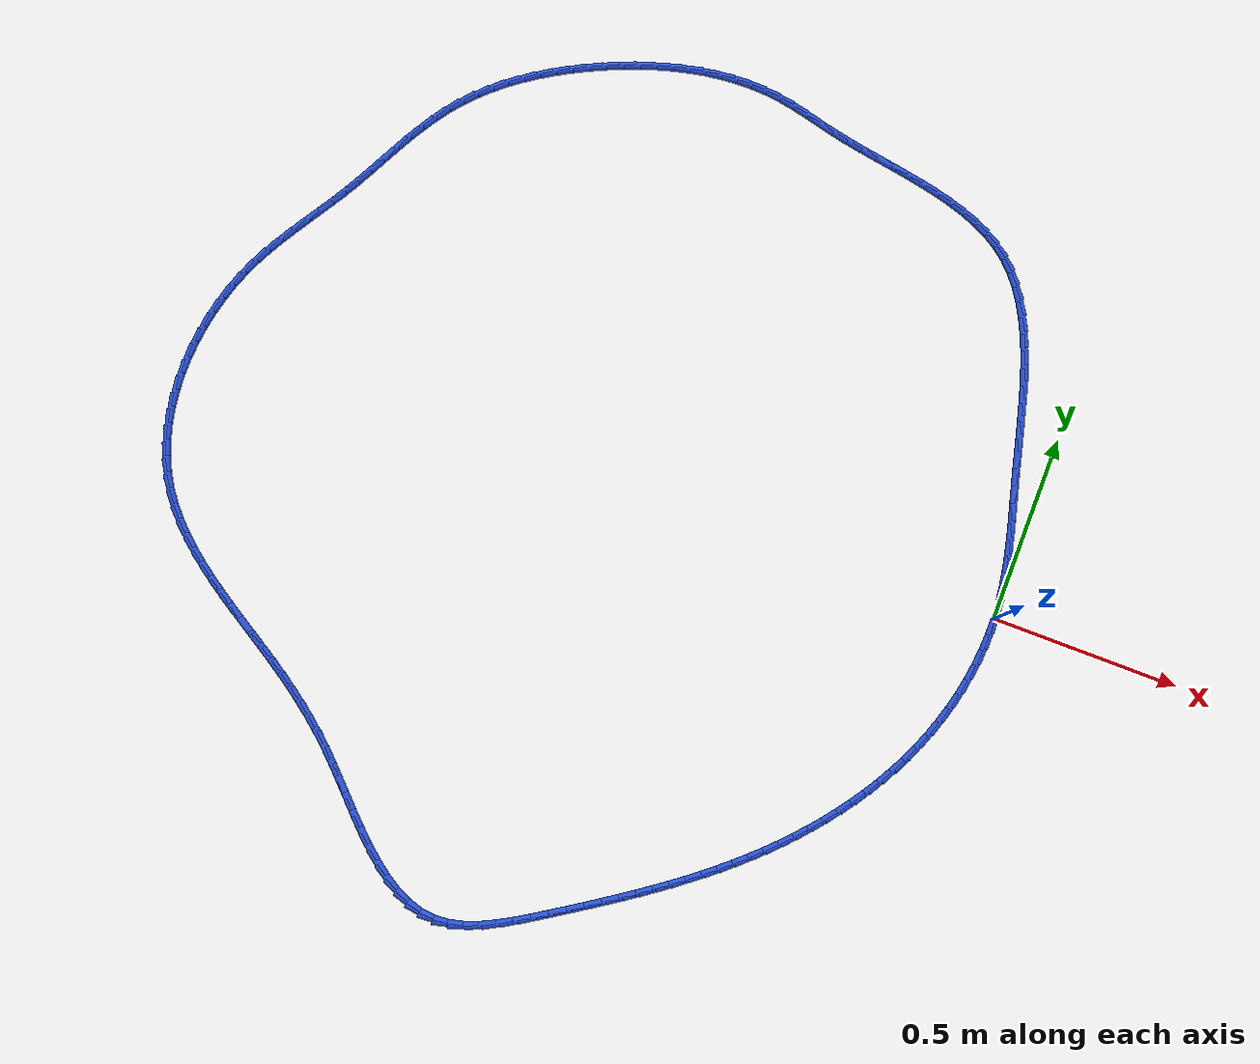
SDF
<sdf version="1.6">
 <world name="default">
  <light name="sun" type="directional">
   <pose>0 0 10 0 -0 0</pose>
   <diffuse>0.8 0.8 0.8 1</diffuse>
   <specular>0.2 0.2 0.2 1</specular>
   <attenuation>
    <range>1000</range>
    <constant>0.9</constant>
    <linear>0.01</linear>
    <quadratic>0.001</quadratic>
   </attenuation>
   <direction>-0.5 0.1 -0.9</direction>
  </light>
  <model name="ground_plane">
   <static>1</static>
   <link name="link">
    <collision name="collision">
     <geometry><plane><normal>0 0 1</normal><size>100 100</size></plane></geometry>
     <surface><friction><ode><mu>100</mu><mu2>50</mu2></ode></friction></surface>
    </collision>
    <visual name="visual">
     <cast_shadows>0</cast_shadows>
     <geometry><plane><normal>0 0 1</normal><size>100 100</size></plane></geometry>
     <material>
      <script><uri>file://media/materials/scripts/gazebo.material</uri><name>Gazebo/WhiteGlow</name></script>
     </material>
    </visual>
   </link>
  </model>
  <gravity>0 0 -9.8</gravity>
  <magnetic_field>6e-06 2.3e-05 -4.2e-05</magnetic_field>
  <atmosphere type="adiabatic"/>
  <physics name="default_physics" default="0" type="ode">
   <max_step_size>0.001</max_step_size>
   <real_time_factor>1</real_time_factor>
   <real_time_update_rate>1000</real_time_update_rate>
  </physics>
  <scene><ambient>0.4 0.4 0.4 1</ambient><background>0.7 0.7 0.7 1</background><shadows>1</shadows></scene>
  <spherical_coordinates>
   <surface_model>EARTH_WGS84</surface_model>
   <latitude_deg>0</latitude_deg>
   <longitude_deg>0</longitude_deg>
   <elevation>0</elevation>
   <heading_deg>0</heading_deg>
  </spherical_coordinates>
  <model name="line">
   <link name="link_0">
    <pose>-1.3877787807814457e-17 -4.163336342344337e-17 0.01 0 1.57 -1.5065889744394763</pose>
    <collision name="collision">
     <geometry><cylinder><radius>0.01</radius><length>0.08</length></cylinder></geometry>
    </collision>
    <visual name="visual">
     <material>
      <script><name>Gazebo/Blue</name><uri>file://media/materials/scripts/gazebo.material</uri></script>
     </material>
     <geometry><cylinder><radius>0.01</radius><length>0.08</length></cylinder></geometry>
    </visual>
   </link>
   <link name="link_1">
    <pose>-0.002736123242575554 0.04255528599908992 0.01 0 1.57 -1.4557629002769725</pose>
    <collision name="collision">
     <geometry><cylinder><radius>0.01</radius><length>0.08</length></cylinder></geometry>
    </collision>
    <visual name="visual">
     <material>
      <script><name>Gazebo/Blue</name><uri>file://media/materials/scripts/gazebo.material</uri></script>
     </material>
     <geometry><cylinder><radius>0.01</radius><length>0.08</length></cylinder></geometry>
    </visual>
   </link>
   <link name="link_2">
    <pose>-0.007618650630001034 0.08481232544572831 0.01 0 1.57 -1.4123592329329906</pose>
    <collision name="collision">
     <geometry><cylinder><radius>0.01</radius><length>0.08</length></cylinder></geometry>
    </collision>
    <visual name="visual">
     <material>
      <script><name>Gazebo/Blue</name><uri>file://media/materials/scripts/gazebo.material</uri></script>
     </material>
     <geometry><cylinder><radius>0.01</radius><length>0.08</length></cylinder></geometry>
    </visual>
   </link>
   <link name="link_3">
    <pose>-0.014345441209843435 0.126913641478169 0.01 0 1.57 -1.3768004767027064</pose>
    <collision name="collision">
     <geometry><cylinder><radius>0.01</radius><length>0.08</length></cylinder></geometry>
    </collision>
    <visual name="visual">
     <material>
      <script><name>Gazebo/Blue</name><uri>file://media/materials/scripts/gazebo.material</uri></script>
     </material>
     <geometry><cylinder><radius>0.01</radius><length>0.08</length></cylinder></geometry>
    </visual>
   </link>
   <link name="link_4">
    <pose>-0.022614354029669693 0.16900175723466565 0.01 0 1.57 -1.3492571074894464</pose>
    <collision name="collision">
     <geometry><cylinder><radius>0.01</radius><length>0.08</length></cylinder></geometry>
    </collision>
    <visual name="visual">
     <material>
      <script><name>Gazebo/Blue</name><uri>file://media/materials/scripts/gazebo.material</uri></script>
     </material>
     <geometry><cylinder><radius>0.01</radius><length>0.08</length></cylinder></geometry>
    </visual>
   </link>
   <link name="link_5">
    <pose>-0.032123248137046805 0.21121919585347218 0.01 0 1.57 -1.3297108356358962</pose>
    <collision name="collision">
     <geometry><cylinder><radius>0.01</radius><length>0.08</length></cylinder></geometry>
    </collision>
    <visual name="visual">
     <material>
      <script><name>Gazebo/Blue</name><uri>file://media/materials/scripts/gazebo.material</uri></script>
     </material>
     <geometry><cylinder><radius>0.01</radius><length>0.08</length></cylinder></geometry>
    </visual>
   </link>
   <link name="link_6">
    <pose>-0.04256998257954175 0.2537084804728424 0.01 0 1.57 -1.3180121047432611</pose>
    <collision name="collision">
     <geometry><cylinder><radius>0.01</radius><length>0.08</length></cylinder></geometry>
    </collision>
    <visual name="visual">
     <material>
      <script><name>Gazebo/Blue</name><uri>file://media/materials/scripts/gazebo.material</uri></script>
     </material>
     <geometry><cylinder><radius>0.01</radius><length>0.08</length></cylinder></geometry>
    </visual>
   </link>
   <link name="link_7">
    <pose>-0.05365241640472146 0.29661213423102994 0.01 0 1.57 -1.3139244283050873</pose>
    <collision name="collision">
     <geometry><cylinder><radius>0.01</radius><length>0.08</length></cylinder></geometry>
    </collision>
    <visual name="visual">
     <material>
      <script><name>Gazebo/Blue</name><uri>file://media/materials/scripts/gazebo.material</uri></script>
     </material>
     <geometry><cylinder><radius>0.01</radius><length>0.08</length></cylinder></geometry>
    </visual>
   </link>
   <link name="link_8">
    <pose>-0.06506840866015291 0.34007268026628873 0.01 0 1.57 -1.3171533033337746</pose>
    <collision name="collision">
     <geometry><cylinder><radius>0.01</radius><length>0.08</length></cylinder></geometry>
    </collision>
    <visual name="visual">
     <material>
      <script><name>Gazebo/Blue</name><uri>file://media/materials/scripts/gazebo.material</uri></script>
     </material>
     <geometry><cylinder><radius>0.01</radius><length>0.08</length></cylinder></geometry>
    </visual>
   </link>
   <link name="link_9">
    <pose>-0.07651582229259807 0.3842326383417553 0.01 0 1.57 -1.324746816008671</pose>
    <collision name="collision">
     <geometry><cylinder><radius>0.01</radius><length>0.08</length></cylinder></geometry>
    </collision>
    <visual name="visual">
     <material>
      <script><name>Gazebo/Blue</name><uri>file://media/materials/scripts/gazebo.material</uri></script>
     </material>
     <geometry><cylinder><radius>0.01</radius><length>0.08</length></cylinder></geometry>
    </visual>
   </link>
   <link name="link_10">
    <pose>-0.08779519151263991 0.4291456566554979 0.01 0 1.57 -1.3272268286062185</pose>
    <collision name="collision">
     <geometry><cylinder><radius>0.01</radius><length>0.08</length></cylinder></geometry>
    </collision>
    <visual name="visual">
     <material>
      <script><name>Gazebo/Blue</name><uri>file://media/materials/scripts/gazebo.material</uri></script>
     </material>
     <geometry><cylinder><radius>0.01</radius><length>0.08</length></cylinder></geometry>
    </visual>
   </link>
   <link name="link_11">
    <pose>-0.0990770961195179 0.47454507439811383 0.01 0 1.57 -1.3226873999227522</pose>
    <collision name="collision">
     <geometry><cylinder><radius>0.01</radius><length>0.08</length></cylinder></geometry>
    </collision>
    <visual name="visual">
     <material>
      <script><name>Gazebo/Blue</name><uri>file://media/materials/scripts/gazebo.material</uri></script>
     </material>
     <geometry><cylinder><radius>0.01</radius><length>0.08</length></cylinder></geometry>
    </visual>
   </link>
   <link name="link_12">
    <pose>-0.11061545497741966 0.5200920930182689 0.01 0 1.57 -1.3111442073078095</pose>
    <collision name="collision">
     <geometry><cylinder><radius>0.01</radius><length>0.08</length></cylinder></geometry>
    </collision>
    <visual name="visual">
     <material>
      <script><name>Gazebo/Blue</name><uri>file://media/materials/scripts/gazebo.material</uri></script>
     </material>
     <geometry><cylinder><radius>0.01</radius><length>0.08</length></cylinder></geometry>
    </visual>
   </link>
   <link name="link_13">
    <pose>-0.12266418695053276 0.565447913964629 0.01 0 1.57 -1.292380234581895</pose>
    <collision name="collision">
     <geometry><cylinder><radius>0.01</radius><length>0.08</length></cylinder></geometry>
    </collision>
    <visual name="visual">
     <material>
      <script><name>Gazebo/Blue</name><uri>file://media/materials/scripts/gazebo.material</uri></script>
     </material>
     <geometry><cylinder><radius>0.01</radius><length>0.08</length></cylinder></geometry>
    </visual>
   </link>
   <link name="link_14">
    <pose>-0.13547721090304488 0.6102737386858604 0.01 0 1.57 -1.2659507250403768</pose>
    <collision name="collision">
     <geometry><cylinder><radius>0.01</radius><length>0.08</length></cylinder></geometry>
    </collision>
    <visual name="visual">
     <material>
      <script><name>Gazebo/Blue</name><uri>file://media/materials/scripts/gazebo.material</uri></script>
     </material>
     <geometry><cylinder><radius>0.01</radius><length>0.08</length></cylinder></geometry>
    </visual>
   </link>
   <link name="link_15">
    <pose>-0.1493084456991436 0.6542307686306286 0.01 0 1.57 -1.2311849095356386</pose>
    <collision name="collision">
     <geometry><cylinder><radius>0.01</radius><length>0.08</length></cylinder></geometry>
    </collision>
    <visual name="visual">
     <material>
      <script><name>Gazebo/Blue</name><uri>file://media/materials/scripts/gazebo.material</uri></script>
     </material>
     <geometry><cylinder><radius>0.01</radius><length>0.08</length></cylinder></geometry>
    </visual>
   </link>
   <link name="link_16">
    <pose>-0.16441181020301654 0.6969802052476001 0.01 0 1.57 -1.1871931929078012</pose>
    <collision name="collision">
     <geometry><cylinder><radius>0.01</radius><length>0.08</length></cylinder></geometry>
    </collision>
    <visual name="visual">
     <material>
      <script><name>Gazebo/Blue</name><uri>file://media/materials/scripts/gazebo.material</uri></script>
     </material>
     <geometry><cylinder><radius>0.01</radius><length>0.08</length></cylinder></geometry>
    </visual>
   </link>
   <link name="link_17">
    <pose>-0.1810412232788513 0.7381832499854408 0.01 0 1.57 -1.132894905399777</pose>
    <collision name="collision">
     <geometry><cylinder><radius>0.01</radius><length>0.08</length></cylinder></geometry>
    </collision>
    <visual name="visual">
     <material>
      <script><name>Gazebo/Blue</name><uri>file://media/materials/scripts/gazebo.material</uri></script>
     </material>
     <geometry><cylinder><radius>0.01</radius><length>0.08</length></cylinder></geometry>
    </visual>
   </link>
   <link name="link_18">
    <pose>-0.19945060379083548 0.7775011042928163 0.01 0 1.57 -1.067091657716847</pose>
    <collision name="collision">
     <geometry><cylinder><radius>0.01</radius><length>0.08</length></cylinder></geometry>
    </collision>
    <visual name="visual">
     <material>
      <script><name>Gazebo/Blue</name><uri>file://media/materials/scripts/gazebo.material</uri></script>
     </material>
     <geometry><cylinder><radius>0.01</radius><length>0.08</length></cylinder></geometry>
    </visual>
   </link>
   <link name="link_19">
    <pose>-0.21989387060315685 0.8145949696183933 0.01 0 1.57 -0.9886233003249689</pose>
    <collision name="collision">
     <geometry><cylinder><radius>0.01</radius><length>0.08</length></cylinder></geometry>
    </collision>
    <visual name="visual">
     <material>
      <script><name>Gazebo/Blue</name><uri>file://media/materials/scripts/gazebo.material</uri></script>
     </material>
     <geometry><cylinder><radius>0.01</radius><length>0.08</length></cylinder></geometry>
    </visual>
   </link>
   <link name="link_20">
    <pose>-0.24262494258000278 0.849126047410837 0.01 0 1.57 -0.896649380838587</pose>
    <collision name="collision">
     <geometry><cylinder><radius>0.01</radius><length>0.08</length></cylinder></geometry>
    </collision>
    <visual name="visual">
     <material>
      <script><name>Gazebo/Blue</name><uri>file://media/materials/scripts/gazebo.material</uri></script>
     </material>
     <geometry><cylinder><radius>0.01</radius><length>0.08</length></cylinder></geometry>
    </visual>
   </link>
   <link name="link_21">
    <pose>-0.26789773858556115 0.8807555391188143 0.01 0 1.57 -0.7910779130215807</pose>
    <collision name="collision">
     <geometry><cylinder><radius>0.01</radius><length>0.08</length></cylinder></geometry>
    </collision>
    <visual name="visual">
     <material>
      <script><name>Gazebo/Blue</name><uri>file://media/materials/scripts/gazebo.material</uri></script>
     </material>
     <geometry><cylinder><radius>0.01</radius><length>0.08</length></cylinder></geometry>
    </visual>
   </link>
   <link name="link_22">
    <pose>-0.2959661774840193 0.9091446461909903 0.01 0 1.57 -0.6738946662018206</pose>
    <collision name="collision">
     <geometry><cylinder><radius>0.01</radius><length>0.08</length></cylinder></geometry>
    </collision>
    <visual name="visual">
     <material>
      <script><name>Gazebo/Blue</name><uri>file://media/materials/scripts/gazebo.material</uri></script>
     </material>
     <geometry><cylinder><radius>0.01</radius><length>0.08</length></cylinder></geometry>
    </visual>
   </link>
   <link name="link_23">
    <pose>-0.3270639339152699 0.9339797201780062 0.01 0 1.57 -0.5603022033302679</pose>
    <collision name="collision">
     <geometry><cylinder><radius>0.01</radius><length>0.08</length></cylinder></geometry>
    </collision>
    <visual name="visual">
     <material>
      <script><name>Gazebo/Blue</name><uri>file://media/materials/scripts/gazebo.material</uri></script>
     </material>
     <geometry><cylinder><radius>0.01</radius><length>0.08</length></cylinder></geometry>
    </visual>
   </link>
   <link name="link_24">
    <pose>-0.36110937552660766 0.9553388294432368 0.01 0 1.57 -0.4623308494250855</pose>
    <collision name="collision">
     <geometry><cylinder><radius>0.01</radius><length>0.08</length></cylinder></geometry>
    </collision>
    <visual name="visual">
     <material>
      <script><name>Gazebo/Blue</name><uri>file://media/materials/scripts/gazebo.material</uri></script>
     </material>
     <geometry><cylinder><radius>0.01</radius><length>0.08</length></cylinder></geometry>
    </visual>
   </link>
   <link name="link_25">
    <pose>-0.3977716470468816 0.9736096606254708 0.01 0 1.57 -0.38055298743751714</pose>
    <collision name="collision">
     <geometry><cylinder><radius>0.01</radius><length>0.08</length></cylinder></geometry>
    </collision>
    <visual name="visual">
     <material>
      <script><name>Gazebo/Blue</name><uri>file://media/materials/scripts/gazebo.material</uri></script>
     </material>
     <geometry><cylinder><radius>0.01</radius><length>0.08</length></cylinder></geometry>
    </visual>
   </link>
   <link name="link_26">
    <pose>-0.43671309541280307 0.9891883454964381 0.01 0 1.57 -0.31413686297920157</pose>
    <collision name="collision">
     <geometry><cylinder><radius>0.01</radius><length>0.08</length></cylinder></geometry>
    </collision>
    <visual name="visual">
     <material>
      <script><name>Gazebo/Blue</name><uri>file://media/materials/scripts/gazebo.material</uri></script>
     </material>
     <geometry><cylinder><radius>0.01</radius><length>0.08</length></cylinder></geometry>
    </visual>
   </link>
   <link name="link_27">
    <pose>-0.4775960675610829 1.0024710158278691 0.01 0 1.57 -0.2617658397699223</pose>
    <collision name="collision">
     <geometry><cylinder><radius>0.01</radius><length>0.08</length></cylinder></geometry>
    </collision>
    <visual name="visual">
     <material>
      <script><name>Gazebo/Blue</name><uri>file://media/materials/scripts/gazebo.material</uri></script>
     </material>
     <geometry><cylinder><radius>0.01</radius><length>0.08</length></cylinder></geometry>
    </visual>
   </link>
   <link name="link_28">
    <pose>-0.5200829104284322 1.0138538033914943 0.01 0 1.57 -0.22206696672779427</pose>
    <collision name="collision">
     <geometry><cylinder><radius>0.01</radius><length>0.08</length></cylinder></geometry>
    </collision>
    <visual name="visual">
     <material>
      <script><name>Gazebo/Blue</name><uri>file://media/materials/scripts/gazebo.material</uri></script>
     </material>
     <geometry><cylinder><radius>0.01</radius><length>0.08</length></cylinder></geometry>
    </visual>
   </link>
   <link name="link_29">
    <pose>-0.5638359709515619 1.023732839959043 0.01 0 1.57 -0.19384427827279066</pose>
    <collision name="collision">
     <geometry><cylinder><radius>0.01</radius><length>0.08</length></cylinder></geometry>
    </collision>
    <visual name="visual">
     <material>
      <script><name>Gazebo/Blue</name><uri>file://media/materials/scripts/gazebo.material</uri></script>
     </material>
     <geometry><cylinder><radius>0.01</radius><length>0.08</length></cylinder></geometry>
    </visual>
   </link>
   <link name="link_30">
    <pose>-0.608517596067183 1.032504257302246 0.01 0 1.57 -0.17618539849086137</pose>
    <collision name="collision">
     <geometry><cylinder><radius>0.01</radius><length>0.08</length></cylinder></geometry>
    </collision>
    <visual name="visual">
     <material>
      <script><name>Gazebo/Blue</name><uri>file://media/materials/scripts/gazebo.material</uri></script>
     </material>
     <geometry><cylinder><radius>0.01</radius><length>0.08</length></cylinder></geometry>
    </visual>
   </link>
   <link name="link_31">
    <pose>-0.6537901327120067 1.0405641871928337 0.01 0 1.57 -0.16850093379170056</pose>
    <collision name="collision">
     <geometry><cylinder><radius>0.01</radius><length>0.08</length></cylinder></geometry>
    </collision>
    <visual name="visual">
     <material>
      <script><name>Gazebo/Blue</name><uri>file://media/materials/scripts/gazebo.material</uri></script>
     </material>
     <geometry><cylinder><radius>0.01</radius><length>0.08</length></cylinder></geometry>
    </visual>
   </link>
   <link name="link_32">
    <pose>-0.6993159278227441 1.048308761402536 0.01 0 1.57 -0.1705348736723597</pose>
    <collision name="collision">
     <geometry><cylinder><radius>0.01</radius><length>0.08</length></cylinder></geometry>
    </collision>
    <visual name="visual">
     <material>
      <script><name>Gazebo/Blue</name><uri>file://media/materials/scripts/gazebo.material</uri></script>
     </material>
     <geometry><cylinder><radius>0.01</radius><length>0.08</length></cylinder></geometry>
    </visual>
   </link>
   <link name="link_33">
    <pose>-0.7447573283361058 1.056134111703083 0.01 0 1.57 -0.18236637135097228</pose>
    <collision name="collision">
     <geometry><cylinder><radius>0.01</radius><length>0.08</length></cylinder></geometry>
    </collision>
    <visual name="visual">
     <material>
      <script><name>Gazebo/Blue</name><uri>file://media/materials/scripts/gazebo.material</uri></script>
     </material>
     <geometry><cylinder><radius>0.01</radius><length>0.08</length></cylinder></geometry>
    </visual>
   </link>
   <link name="link_34">
    <pose>-0.7897766811888035 1.064436369866205 0.01 0 1.57 -0.2044107261290354</pose>
    <collision name="collision">
     <geometry><cylinder><radius>0.01</radius><length>0.08</length></cylinder></geometry>
    </collision>
    <visual name="visual">
     <material>
      <script><name>Gazebo/Blue</name><uri>file://media/materials/scripts/gazebo.material</uri></script>
     </material>
     <geometry><cylinder><radius>0.01</radius><length>0.08</length></cylinder></geometry>
    </visual>
   </link>
   <link name="link_35">
    <pose>-0.8340363333175475 1.0736116676636323 0.01 0 1.57 -0.2337162961836797</pose>
    <collision name="collision">
     <geometry><cylinder><radius>0.01</radius><length>0.08</length></cylinder></geometry>
    </collision>
    <visual name="visual">
     <material>
      <script><name>Gazebo/Blue</name><uri>file://media/materials/scripts/gazebo.material</uri></script>
     </material>
     <geometry><cylinder><radius>0.01</radius><length>0.08</length></cylinder></geometry>
    </visual>
   </link>
   <link name="link_36">
    <pose>-0.8772731666122037 1.0839049234844345 0.01 0 1.57 -0.24590115572909568</pose>
    <collision name="collision">
     <geometry><cylinder><radius>0.01</radius><length>0.08</length></cylinder></geometry>
    </collision>
    <visual name="visual">
     <material>
      <script><name>Gazebo/Blue</name><uri>file://media/materials/scripts/gazebo.material</uri></script>
     </material>
     <geometry><cylinder><radius>0.01</radius><length>0.08</length></cylinder></geometry>
    </visual>
   </link>
   <link name="link_37">
    <pose>-0.9197185409943457 1.0945578794539088 0.01 0 1.57 -0.2298114242213437</pose>
    <collision name="collision">
     <geometry><cylinder><radius>0.01</radius><length>0.08</length></cylinder></geometry>
    </collision>
    <visual name="visual">
     <material>
      <script><name>Gazebo/Blue</name><uri>file://media/materials/scripts/gazebo.material</uri></script>
     </material>
     <geometry><cylinder><radius>0.01</radius><length>0.08</length></cylinder></geometry>
    </visual>
   </link>
   <link name="link_38">
    <pose>-0.9618051553782825 1.104403809604671 0.01 0 1.57 -0.1845636689146464</pose>
    <collision name="collision">
     <geometry><cylinder><radius>0.01</radius><length>0.08</length></cylinder></geometry>
    </collision>
    <visual name="visual">
     <material>
      <script><name>Gazebo/Blue</name><uri>file://media/materials/scripts/gazebo.material</uri></script>
     </material>
     <geometry><cylinder><radius>0.01</radius><length>0.08</length></cylinder></geometry>
    </visual>
   </link>
   <link name="link_39">
    <pose>-1.0039662947822876 1.1122747996015632 0.01 0 1.57 -0.1161353624137754</pose>
    <collision name="collision">
     <geometry><cylinder><radius>0.01</radius><length>0.08</length></cylinder></geometry>
    </collision>
    <visual name="visual">
     <material>
      <script><name>Gazebo/Blue</name><uri>file://media/materials/scripts/gazebo.material</uri></script>
     </material>
     <geometry><cylinder><radius>0.01</radius><length>0.08</length></cylinder></geometry>
    </visual>
   </link>
   <link name="link_40">
    <pose>-1.0465375420974667 1.1172411748058297 0.01 0 1.57 -0.046805380459156457</pose>
    <collision name="collision">
     <geometry><cylinder><radius>0.01</radius><length>0.08</length></cylinder></geometry>
    </collision>
    <visual name="visual">
     <material>
      <script><name>Gazebo/Blue</name><uri>file://media/materials/scripts/gazebo.material</uri></script>
     </material>
     <geometry><cylinder><radius>0.01</radius><length>0.08</length></cylinder></geometry>
    </visual>
   </link>
   <link name="link_41">
    <pose>-1.0894936090137264 1.1192532193667835 0.01 0 1.57 0.018245535377048705</pose>
    <collision name="collision">
     <geometry><cylinder><radius>0.01</radius><length>0.08</length></cylinder></geometry>
    </collision>
    <visual name="visual">
     <material>
      <script><name>Gazebo/Blue</name><uri>file://media/materials/scripts/gazebo.material</uri></script>
     </material>
     <geometry><cylinder><radius>0.01</radius><length>0.08</length></cylinder></geometry>
    </visual>
   </link>
   <link name="link_42">
    <pose>-1.1327259085297152 1.1184643353748789 0.01 0 1.57 0.07901521152322846</pose>
    <collision name="collision">
     <geometry><cylinder><radius>0.01</radius><length>0.08</length></cylinder></geometry>
    </collision>
    <visual name="visual">
     <material>
      <script><name>Gazebo/Blue</name><uri>file://media/materials/scripts/gazebo.material</uri></script>
     </material>
     <geometry><cylinder><radius>0.01</radius><length>0.08</length></cylinder></geometry>
    </visual>
   </link>
   <link name="link_43">
    <pose>-1.1761258536440833 1.1150279249205708 0.01 0 1.57 0.13562500944360437</pose>
    <collision name="collision">
     <geometry><cylinder><radius>0.01</radius><length>0.08</length></cylinder></geometry>
    </collision>
    <visual name="visual">
     <material>
      <script><name>Gazebo/Blue</name><uri>file://media/materials/scripts/gazebo.material</uri></script>
     </material>
     <geometry><cylinder><radius>0.01</radius><length>0.08</length></cylinder></geometry>
    </visual>
   </link>
   <link name="link_44">
    <pose>-1.2195848573554806 1.1090973900943142 0.01 0 1.57 0.18828342869265816</pose>
    <collision name="collision">
     <geometry><cylinder><radius>0.01</radius><length>0.08</length></cylinder></geometry>
    </collision>
    <visual name="visual">
     <material>
      <script><name>Gazebo/Blue</name><uri>file://media/materials/scripts/gazebo.material</uri></script>
     </material>
     <geometry><cylinder><radius>0.01</radius><length>0.08</length></cylinder></geometry>
    </visual>
   </link>
   <link name="link_45">
    <pose>-1.2629943326625563 1.100826132986564 0.01 0 1.57 0.23725495494865165</pose>
    <collision name="collision">
     <geometry><cylinder><radius>0.01</radius><length>0.08</length></cylinder></geometry>
    </collision>
    <visual name="visual">
     <material>
      <script><name>Gazebo/Blue</name><uri>file://media/materials/scripts/gazebo.material</uri></script>
     </material>
     <geometry><cylinder><radius>0.01</radius><length>0.08</length></cylinder></geometry>
    </visual>
   </link>
   <link name="link_46">
    <pose>-1.3062456925639614 1.090367555687776 0.01 0 1.57 0.2828355421100429</pose>
    <collision name="collision">
     <geometry><cylinder><radius>0.01</radius><length>0.08</length></cylinder></geometry>
    </collision>
    <visual name="visual">
     <material>
      <script><name>Gazebo/Blue</name><uri>file://media/materials/scripts/gazebo.material</uri></script>
     </material>
     <geometry><cylinder><radius>0.01</radius><length>0.08</length></cylinder></geometry>
    </visual>
   </link>
   <link name="link_47">
    <pose>-1.3492303500583431 1.0778750602884037 0.01 0 1.57 0.3253346610172963</pose>
    <collision name="collision">
     <geometry><cylinder><radius>0.01</radius><length>0.08</length></cylinder></geometry>
    </collision>
    <visual name="visual">
     <material>
      <script><name>Gazebo/Blue</name><uri>file://media/materials/scripts/gazebo.material</uri></script>
     </material>
     <geometry><cylinder><radius>0.01</radius><length>0.08</length></cylinder></geometry>
    </visual>
   </link>
   <link name="link_48">
    <pose>-1.3918397181443536 1.0635020488789035 0.01 0 1.57 0.36506308783761415</pose>
    <collision name="collision">
     <geometry><cylinder><radius>0.01</radius><length>0.08</length></cylinder></geometry>
    </collision>
    <visual name="visual">
     <material>
      <script><name>Gazebo/Blue</name><uri>file://media/materials/scripts/gazebo.material</uri></script>
     </material>
     <geometry><cylinder><radius>0.01</radius><length>0.08</length></cylinder></geometry>
    </visual>
   </link>
   <link name="link_49">
    <pose>-1.433965209820641 1.0474019235497294 0.01 0 1.57 0.40232534033141276</pose>
    <collision name="collision">
     <geometry><cylinder><radius>0.01</radius><length>0.08</length></cylinder></geometry>
    </collision>
    <visual name="visual">
     <material>
      <script><name>Gazebo/Blue</name><uri>file://media/materials/scripts/gazebo.material</uri></script>
     </material>
     <geometry><cylinder><radius>0.01</radius><length>0.08</length></cylinder></geometry>
    </visual>
   </link>
   <link name="link_50">
    <pose>-1.4754982380858557 1.0297280863913367 0.01 0 1.57 0.43742130008491203</pose>
    <collision name="collision">
     <geometry><cylinder><radius>0.01</radius><length>0.08</length></cylinder></geometry>
    </collision>
    <visual name="visual">
     <material>
      <script><name>Gazebo/Blue</name><uri>file://media/materials/scripts/gazebo.material</uri></script>
     </material>
     <geometry><cylinder><radius>0.01</radius><length>0.08</length></cylinder></geometry>
    </visual>
   </link>
   <link name="link_51">
    <pose>-1.5163301417807962 1.0106336953747097 0.01 0 1.57 0.4720263052613336</pose>
    <collision name="collision">
     <geometry><cylinder><radius>0.01</radius><length>0.08</length></cylinder></geometry>
    </collision>
    <visual name="visual">
     <material>
      <script><name>Gazebo/Blue</name><uri>file://media/materials/scripts/gazebo.material</uri></script>
     </material>
     <geometry><cylinder><radius>0.01</radius><length>0.08</length></cylinder></geometry>
    </visual>
   </link>
   <link name="link_52">
    <pose>-1.556333794640535 0.9902111233785597 0.01 0 1.57 0.5096207646614486</pose>
    <collision name="collision">
     <geometry><cylinder><radius>0.01</radius><length>0.08</length></cylinder></geometry>
    </collision>
    <visual name="visual">
     <material>
      <script><name>Gazebo/Blue</name><uri>file://media/materials/scripts/gazebo.material</uri></script>
     </material>
     <geometry><cylinder><radius>0.01</radius><length>0.08</length></cylinder></geometry>
    </visual>
   </link>
   <link name="link_53">
    <pose>-1.5953394356988375 0.9684123945453553 0.01 0 1.57 0.5509156720878879</pose>
    <collision name="collision">
     <geometry><cylinder><radius>0.01</radius><length>0.08</length></cylinder></geometry>
    </collision>
    <visual name="visual">
     <material>
      <script><name>Gazebo/Blue</name><uri>file://media/materials/scripts/gazebo.material</uri></script>
     </material>
     <geometry><cylinder><radius>0.01</radius><length>0.08</length></cylinder></geometry>
    </visual>
   </link>
   <link name="link_54">
    <pose>-1.6331713058105042 0.9451697876737174 0.01 0 1.57 0.5961678447784188</pose>
    <collision name="collision">
     <geometry><cylinder><radius>0.01</radius><length>0.08</length></cylinder></geometry>
    </collision>
    <visual name="visual">
     <material>
      <script><name>Gazebo/Blue</name><uri>file://media/materials/scripts/gazebo.material</uri></script>
     </material>
     <geometry><cylinder><radius>0.01</radius><length>0.08</length></cylinder></geometry>
    </visual>
   </link>
   <link name="link_55">
    <pose>-1.6696536458303373 0.9204155815622662 0.01 0 1.57 0.6456167042172013</pose>
    <collision name="collision">
     <geometry><cylinder><radius>0.01</radius><length>0.08</length></cylinder></geometry>
    </collision>
    <visual name="visual">
     <material>
      <script><name>Gazebo/Blue</name><uri>file://media/materials/scripts/gazebo.material</uri></script>
     </material>
     <geometry><cylinder><radius>0.01</radius><length>0.08</length></cylinder></geometry>
    </visual>
   </link>
   <link name="link_56">
    <pose>-1.7046106966131378 0.8940820550096213 0.01 0 1.57 0.6994619111537682</pose>
    <collision name="collision">
     <geometry><cylinder><radius>0.01</radius><length>0.08</length></cylinder></geometry>
    </collision>
    <visual name="visual">
     <material>
      <script><name>Gazebo/Blue</name><uri>file://media/materials/scripts/gazebo.material</uri></script>
     </material>
     <geometry><cylinder><radius>0.01</radius><length>0.08</length></cylinder></geometry>
    </visual>
   </link>
   <link name="link_57">
    <pose>-1.7378666990137064 0.8661014868144038 0.01 0 1.57 0.7578345049695046</pose>
    <collision name="collision">
     <geometry><cylinder><radius>0.01</radius><length>0.08</length></cylinder></geometry>
    </collision>
    <visual name="visual">
     <material>
      <script><name>Gazebo/Blue</name><uri>file://media/materials/scripts/gazebo.material</uri></script>
     </material>
     <geometry><cylinder><radius>0.01</radius><length>0.08</length></cylinder></geometry>
    </visual>
   </link>
   <link name="link_58">
    <pose>-1.7692458938868452 0.8364061557752331 0.01 0 1.57 0.8207621914939826</pose>
    <collision name="collision">
     <geometry><cylinder><radius>0.01</radius><length>0.08</length></cylinder></geometry>
    </collision>
    <visual name="visual">
     <material>
      <script><name>Gazebo/Blue</name><uri>file://media/materials/scripts/gazebo.material</uri></script>
     </material>
     <geometry><cylinder><radius>0.01</radius><length>0.08</length></cylinder></geometry>
    </visual>
   </link>
   <link name="link_59">
    <pose>-1.7985725220873552 0.8049283406907304 0.01 0 1.57 0.8880378276672072</pose>
    <collision name="collision">
     <geometry><cylinder><radius>0.01</radius><length>0.08</length></cylinder></geometry>
    </collision>
    <visual name="visual">
     <material>
      <script><name>Gazebo/Blue</name><uri>file://media/materials/scripts/gazebo.material</uri></script>
     </material>
     <geometry><cylinder><radius>0.01</radius><length>0.08</length></cylinder></geometry>
    </visual>
   </link>
   <link name="link_60">
    <pose>-1.8256741652945834 0.7716025764746027 0.01 0 1.57 0.9532823478440139</pose>
    <collision name="collision">
     <geometry><cylinder><radius>0.01</radius><length>0.08</length></cylinder></geometry>
    </collision>
    <visual name="visual">
     <material>
      <script><name>Gazebo/Blue</name><uri>file://media/materials/scripts/gazebo.material</uri></script>
     </material>
     <geometry><cylinder><radius>0.01</radius><length>0.08</length></cylinder></geometry>
    </visual>
   </link>
   <link name="link_61">
    <pose>-1.8505955649050656 0.7365100496553411 0.01 0 1.57 1.006463212726291</pose>
    <collision name="collision">
     <geometry><cylinder><radius>0.01</radius><length>0.08</length></cylinder></geometry>
    </collision>
    <visual name="visual">
     <material>
      <script><name>Gazebo/Blue</name><uri>file://media/materials/scripts/gazebo.material</uri></script>
     </material>
     <geometry><cylinder><radius>0.01</radius><length>0.08</length></cylinder></geometry>
    </visual>
   </link>
   <link name="link_62">
    <pose>-1.873728036955021 0.699965994453203 0.01 0 1.57 1.0467356057580637</pose>
    <collision name="collision">
     <geometry><cylinder><radius>0.01</radius><length>0.08</length></cylinder></geometry>
    </collision>
    <visual name="visual">
     <material>
      <script><name>Gazebo/Blue</name><uri>file://media/materials/scripts/gazebo.material</uri></script>
     </material>
     <geometry><cylinder><radius>0.01</radius><length>0.08</length></cylinder></geometry>
    </visual>
   </link>
   <link name="link_63">
    <pose>-1.8954939077282846 0.662306586830986 0.01 0 1.57 1.0743595727182282</pose>
    <collision name="collision">
     <geometry><cylinder><radius>0.01</radius><length>0.08</length></cylinder></geometry>
    </collision>
    <visual name="visual">
     <material>
      <script><name>Gazebo/Blue</name><uri>file://media/materials/scripts/gazebo.material</uri></script>
     </material>
     <geometry><cylinder><radius>0.01</radius><length>0.08</length></cylinder></geometry>
    </visual>
   </link>
   <link name="link_64">
    <pose>-1.91631550350869 0.6238680027514886 0.01 0 1.57 1.0896340880028401</pose>
    <collision name="collision">
     <geometry><cylinder><radius>0.01</radius><length>0.08</length></cylinder></geometry>
    </collision>
    <visual name="visual">
     <material>
      <script><name>Gazebo/Blue</name><uri>file://media/materials/scripts/gazebo.material</uri></script>
     </material>
     <geometry><cylinder><radius>0.01</radius><length>0.08</length></cylinder></geometry>
    </visual>
   </link>
   <link name="link_65">
    <pose>-1.9366151505800715 0.5849864181775083 0.01 0 1.57 1.0927711632133499</pose>
    <collision name="collision">
     <geometry><cylinder><radius>0.01</radius><length>0.08</length></cylinder></geometry>
    </collision>
    <visual name="visual">
     <material>
      <script><name>Gazebo/Blue</name><uri>file://media/materials/scripts/gazebo.material</uri></script>
     </material>
     <geometry><cylinder><radius>0.01</radius><length>0.08</length></cylinder></geometry>
    </visual>
   </link>
   <link name="link_66">
    <pose>-1.9568151752262648 0.5459980090718431 0.01 0 1.57 1.0838320582885155</pose>
    <collision name="collision">
     <geometry><cylinder><radius>0.01</radius><length>0.08</length></cylinder></geometry>
    </collision>
    <visual name="visual">
     <material>
      <script><name>Gazebo/Blue</name><uri>file://media/materials/scripts/gazebo.material</uri></script>
     </material>
     <geometry><cylinder><radius>0.01</radius><length>0.08</length></cylinder></geometry>
    </visual>
   </link>
   <link name="link_67">
    <pose>-1.9773379037311036 0.5072389513972912 0.01 0 1.57 1.0627174661478553</pose>
    <collision name="collision">
     <geometry><cylinder><radius>0.01</radius><length>0.08</length></cylinder></geometry>
    </collision>
    <visual name="visual">
     <material>
      <script><name>Gazebo/Blue</name><uri>file://media/materials/scripts/gazebo.material</uri></script>
     </material>
     <geometry><cylinder><radius>0.01</radius><length>0.08</length></cylinder></geometry>
    </visual>
   </link>
   <link name="link_68">
    <pose>-1.998605589356477 0.4690453651865532 0.01 0 1.57 1.0343805173795573</pose>
    <collision name="collision">
     <geometry><cylinder><radius>0.01</radius><length>0.08</length></cylinder></geometry>
    </collision>
    <visual name="visual">
     <material>
      <script><name>Gazebo/Blue</name><uri>file://media/materials/scripts/gazebo.material</uri></script>
     </material>
     <geometry><cylinder><radius>0.01</radius><length>0.08</length></cylinder></geometry>
    </visual>
   </link>
   <link name="link_69">
    <pose>-2.0208602811884546 0.4316153457052754 0.01 0 1.57 1.0151057497956326</pose>
    <collision name="collision">
     <geometry><cylinder><radius>0.01</radius><length>0.08</length></cylinder></geometry>
    </collision>
    <visual name="visual">
     <material>
      <script><name>Gazebo/Blue</name><uri>file://media/materials/scripts/gazebo.material</uri></script>
     </material>
     <geometry><cylinder><radius>0.01</radius><length>0.08</length></cylinder></geometry>
    </visual>
   </link>
   <link name="link_70">
    <pose>-2.0437759475881565 0.3947118750516446 0.01 0 1.57 1.0082530462812844</pose>
    <collision name="collision">
     <geometry><cylinder><radius>0.01</radius><length>0.08</length></cylinder></geometry>
    </collision>
    <visual name="visual">
     <material>
      <script><name>Gazebo/Blue</name><uri>file://media/materials/scripts/gazebo.material</uri></script>
     </material>
     <geometry><cylinder><radius>0.01</radius><length>0.08</length></cylinder></geometry>
    </visual>
   </link>
   <link name="link_71">
    <pose>-2.066914893659993 0.35801240847672416 0.01 0 1.57 1.013892625373761</pose>
    <collision name="collision">
     <geometry><cylinder><radius>0.01</radius><length>0.08</length></cylinder></geometry>
    </collision>
    <visual name="visual">
     <material>
      <script><name>Gazebo/Blue</name><uri>file://media/materials/scripts/gazebo.material</uri></script>
     </material>
     <geometry><cylinder><radius>0.01</radius><length>0.08</length></cylinder></geometry>
    </visual>
   </link>
   <link name="link_72">
    <pose>-2.08983942450837 0.3211944012315787 0.01 0 1.57 1.0320170995414375</pose>
    <collision name="collision">
     <geometry><cylinder><radius>0.01</radius><length>0.08</length></cylinder></geometry>
    </collision>
    <visual name="visual">
     <material>
      <script><name>Gazebo/Blue</name><uri>file://media/materials/scripts/gazebo.material</uri></script>
     </material>
     <geometry><cylinder><radius>0.01</radius><length>0.08</length></cylinder></geometry>
    </visual>
   </link>
   <link name="link_73">
    <pose>-2.1121118452376972 0.283935308567271 0.01 0 1.57 1.0625152599636731</pose>
    <collision name="collision">
     <geometry><cylinder><radius>0.01</radius><length>0.08</length></cylinder></geometry>
    </collision>
    <visual name="visual">
     <material>
      <script><name>Gazebo/Blue</name><uri>file://media/materials/scripts/gazebo.material</uri></script>
     </material>
     <geometry><cylinder><radius>0.01</radius><length>0.08</length></cylinder></geometry>
    </visual>
   </link>
   <link name="link_74">
    <pose>-2.133294460952383 0.24591258573486557 0.01 0 1.57 1.105091625869532</pose>
    <collision name="collision">
     <geometry><cylinder><radius>0.01</radius><length>0.08</length></cylinder></geometry>
    </collision>
    <visual name="visual">
     <material>
      <script><name>Gazebo/Blue</name><uri>file://media/materials/scripts/gazebo.material</uri></script>
     </material>
     <geometry><cylinder><radius>0.01</radius><length>0.08</length></cylinder></geometry>
    </visual>
   </link>
   <link name="link_75">
    <pose>-2.1529495767568356 0.2068036879854258 0.01 0 1.57 1.1591406686309906</pose>
    <collision name="collision">
     <geometry><cylinder><radius>0.01</radius><length>0.08</length></cylinder></geometry>
    </collision>
    <visual name="visual">
     <material>
      <script><name>Gazebo/Blue</name><uri>file://media/materials/scripts/gazebo.material</uri></script>
     </material>
     <geometry><cylinder><radius>0.01</radius><length>0.08</length></cylinder></geometry>
    </visual>
   </link>
   <link name="link_76">
    <pose>-2.1706395621715195 0.16628618190273534 0.01 0 1.57 1.2208725332978312</pose>
    <collision name="collision">
     <geometry><cylinder><radius>0.01</radius><length>0.08</length></cylinder></geometry>
    </collision>
    <visual name="visual">
     <material>
      <script><name>Gazebo/Blue</name><uri>file://media/materials/scripts/gazebo.material</uri></script>
     </material>
     <geometry><cylinder><radius>0.01</radius><length>0.08</length></cylinder></geometry>
    </visual>
   </link>
   <link name="link_77">
    <pose>-2.1860071493092126 0.12417652779787522 0.01 0 1.57 1.2818208759926466</pose>
    <collision name="collision">
     <geometry><cylinder><radius>0.01</radius><length>0.08</length></cylinder></geometry>
    </collision>
    <visual name="visual">
     <material>
      <script><name>Gazebo/Blue</name><uri>file://media/materials/scripts/gazebo.material</uri></script>
     </material>
     <geometry><cylinder><radius>0.01</radius><length>0.08</length></cylinder></geometry>
    </visual>
   </link>
   <link name="link_78">
    <pose>-2.1989322662786344 0.0807011408505647 0.01 0 1.57 1.3412750732800531</pose>
    <collision name="collision">
     <geometry><cylinder><radius>0.01</radius><length>0.08</length></cylinder></geometry>
    </collision>
    <visual name="visual">
     <material>
      <script><name>Gazebo/Blue</name><uri>file://media/materials/scripts/gazebo.material</uri></script>
     </material>
     <geometry><cylinder><radius>0.01</radius><length>0.08</length></cylinder></geometry>
    </visual>
   </link>
   <link name="link_79">
    <pose>-2.2093383902587376 0.03616170375629976 0.01 0 1.57 1.4000621397140474</pose>
    <collision name="collision">
     <geometry><cylinder><radius>0.01</radius><length>0.08</length></cylinder></geometry>
    </collision>
    <visual name="visual">
     <material>
      <script><name>Gazebo/Blue</name><uri>file://media/materials/scripts/gazebo.material</uri></script>
     </material>
     <geometry><cylinder><radius>0.01</radius><length>0.08</length></cylinder></geometry>
    </visual>
   </link>
   <link name="link_80">
    <pose>-2.217148998428473 -0.00914010078942517 0.01 0 1.57 1.4589769109114703</pose>
    <collision name="collision">
     <geometry><cylinder><radius>0.01</radius><length>0.08</length></cylinder></geometry>
    </collision>
    <visual name="visual">
     <material>
      <script><name>Gazebo/Blue</name><uri>file://media/materials/scripts/gazebo.material</uri></script>
     </material>
     <geometry><cylinder><radius>0.01</radius><length>0.08</length></cylinder></geometry>
    </visual>
   </link>
   <link name="link_81">
    <pose>-2.2222875679667924 -0.05490259009111516 0.01 0 1.57 1.5187977189964648</pose>
    <collision name="collision">
     <geometry><cylinder><radius>0.01</radius><length>0.08</length></cylinder></geometry>
    </collision>
    <visual name="visual">
     <material>
      <script><name>Gazebo/Blue</name><uri>file://media/materials/scripts/gazebo.material</uri></script>
     </material>
     <geometry><cylinder><radius>0.01</radius><length>0.08</length></cylinder></geometry>
    </visual>
   </link>
   <link name="link_82">
    <pose>-2.2246775760526476 -0.10082408145327608 0.01 0 1.57 -1.5612927358926931</pose>
    <collision name="collision">
     <geometry><cylinder><radius>0.01</radius><length>0.08</length></cylinder></geometry>
    </collision>
    <visual name="visual">
     <material>
      <script><name>Gazebo/Blue</name><uri>file://media/materials/scripts/gazebo.material</uri></script>
     </material>
     <geometry><cylinder><radius>0.01</radius><length>0.08</length></cylinder></geometry>
    </visual>
   </link>
   <link name="link_83">
    <pose>-2.22424249986499 -0.14660289218041134 0.01 0 1.57 -1.4973273017403008</pose>
    <collision name="collision">
     <geometry><cylinder><radius>0.01</radius><length>0.08</length></cylinder></geometry>
    </collision>
    <visual name="visual">
     <material>
      <script><name>Gazebo/Blue</name><uri>file://media/materials/scripts/gazebo.material</uri></script>
     </material>
     <geometry><cylinder><radius>0.01</radius><length>0.08</length></cylinder></geometry>
    </visual>
   </link>
   <link name="link_84">
    <pose>-2.2209058165827713 -0.1919373395770268 0.01 0 1.57 -1.4301074008903827</pose>
    <collision name="collision">
     <geometry><cylinder><radius>0.01</radius><length>0.08</length></cylinder></geometry>
    </collision>
    <visual name="visual">
     <material>
      <script><name>Gazebo/Blue</name><uri>file://media/materials/scripts/gazebo.material</uri></script>
     </material>
     <geometry><cylinder><radius>0.01</radius><length>0.08</length></cylinder></geometry>
    </visual>
   </link>
   <link name="link_85">
    <pose>-2.2145910033849425 -0.23652574094762743 0.01 0 1.57 -1.358839697114405</pose>
    <collision name="collision">
     <geometry><cylinder><radius>0.01</radius><length>0.08</length></cylinder></geometry>
    </collision>
    <visual name="visual">
     <material>
      <script><name>Gazebo/Blue</name><uri>file://media/materials/scripts/gazebo.material</uri></script>
     </material>
     <geometry><cylinder><radius>0.01</radius><length>0.08</length></cylinder></geometry>
    </visual>
   </link>
   <link name="link_86">
    <pose>-2.205221537450456 -0.28006641359671847 0.01 0 1.57 -1.282751184687003</pose>
    <collision name="collision">
     <geometry><cylinder><radius>0.01</radius><length>0.08</length></cylinder></geometry>
    </collision>
    <visual name="visual">
     <material>
      <script><name>Gazebo/Blue</name><uri>file://media/materials/scripts/gazebo.material</uri></script>
     </material>
     <geometry><cylinder><radius>0.01</radius><length>0.08</length></cylinder></geometry>
    </visual>
   </link>
   <link name="link_87">
    <pose>-2.192720895958263 -0.32225767482880563 0.01 0 1.57 -1.2011329461596805</pose>
    <collision name="collision">
     <geometry><cylinder><radius>0.01</radius><length>0.08</length></cylinder></geometry>
    </collision>
    <visual name="visual">
     <material>
      <script><name>Gazebo/Blue</name><uri>file://media/materials/scripts/gazebo.material</uri></script>
     </material>
     <geometry><cylinder><radius>0.01</radius><length>0.08</length></cylinder></geometry>
    </visual>
   </link>
   <link name="link_88">
    <pose>-2.1770125560873153 -0.3627978419483924 0.01 0 1.57 -1.1134113458932742</pose>
    <collision name="collision">
     <geometry><cylinder><radius>0.01</radius><length>0.08</length></cylinder></geometry>
    </collision>
    <visual name="visual">
     <material>
      <script><name>Gazebo/Blue</name><uri>file://media/materials/scripts/gazebo.material</uri></script>
     </material>
     <geometry><cylinder><radius>0.01</radius><length>0.08</length></cylinder></geometry>
    </visual>
   </link>
   <link name="link_89">
    <pose>-2.158019995016565 -0.4013852322599847 0.01 0 1.57 -1.0200822075237066</pose>
    <collision name="collision">
     <geometry><cylinder><radius>0.01</radius><length>0.08</length></cylinder></geometry>
    </collision>
    <visual name="visual">
     <material>
      <script><name>Gazebo/Blue</name><uri>file://media/materials/scripts/gazebo.material</uri></script>
     </material>
     <geometry><cylinder><radius>0.01</radius><length>0.08</length></cylinder></geometry>
    </visual>
   </link>
   <link name="link_90">
    <pose>-2.135690768168279 -0.4377468280054601 0.01 0 1.57 -0.9301320109180112</pose>
    <collision name="collision">
     <geometry><cylinder><radius>0.01</radius><length>0.08</length></cylinder></geometry>
    </collision>
    <visual name="visual">
     <material>
      <script><name>Gazebo/Blue</name><uri>file://media/materials/scripts/gazebo.material</uri></script>
     </material>
     <geometry><cylinder><radius>0.01</radius><length>0.08</length></cylinder></geometry>
    </visual>
   </link>
   <link name="link_91">
    <pose>-2.1102219685225387 -0.47190668369948147 0.01 0 1.57 -0.849761670238242</pose>
    <collision name="collision">
     <geometry><cylinder><radius>0.01</radius><length>0.08</length></cylinder></geometry>
    </collision>
    <visual name="visual">
     <material>
      <script><name>Gazebo/Blue</name><uri>file://media/materials/scripts/gazebo.material</uri></script>
     </material>
     <geometry><cylinder><radius>0.01</radius><length>0.08</length></cylinder></geometry>
    </visual>
   </link>
   <link name="link_92">
    <pose>-2.0819583422183654 -0.5040646336467166 0.01 0 1.57 -0.779607973971404</pose>
    <collision name="collision">
     <geometry><cylinder><radius>0.01</radius><length>0.08</length></cylinder></geometry>
    </collision>
    <visual name="visual">
     <material>
      <script><name>Gazebo/Blue</name><uri>file://media/materials/scripts/gazebo.material</uri></script>
     </material>
     <geometry><cylinder><radius>0.01</radius><length>0.08</length></cylinder></geometry>
    </visual>
   </link>
   <link name="link_93">
    <pose>-2.0512465608878654 -0.5344228044344534 0.01 0 1.57 -0.7196736120943518</pose>
    <collision name="collision">
     <geometry><cylinder><radius>0.01</radius><length>0.08</length></cylinder></geometry>
    </collision>
    <visual name="visual">
     <material>
      <script><name>Gazebo/Blue</name><uri>file://media/materials/scripts/gazebo.material</uri></script>
     </material>
     <geometry><cylinder><radius>0.01</radius><length>0.08</length></cylinder></geometry>
    </visual>
   </link>
   <link name="link_94">
    <pose>-2.0184332961631455 -0.5631833226499818 0.01 0 1.57 -0.66961401940539</pose>
    <collision name="collision">
     <geometry><cylinder><radius>0.01</radius><length>0.08</length></cylinder></geometry>
    </collision>
    <visual name="visual">
     <material>
      <script><name>Gazebo/Blue</name><uri>file://media/materials/scripts/gazebo.material</uri></script>
     </material>
     <geometry><cylinder><radius>0.01</radius><length>0.08</length></cylinder></geometry>
    </visual>
   </link>
   <link name="link_95">
    <pose>-1.9838652196763134 -0.5905483148805909 0.01 0 1.57 -0.6289248383860808</pose>
    <collision name="collision">
     <geometry><cylinder><radius>0.01</radius><length>0.08</length></cylinder></geometry>
    </collision>
    <visual name="visual">
     <material>
      <script><name>Gazebo/Blue</name><uri>file://media/materials/scripts/gazebo.material</uri></script>
     </material>
     <geometry><cylinder><radius>0.01</radius><length>0.08</length></cylinder></geometry>
    </visual>
   </link>
   <link name="link_96">
    <pose>-1.9478890030594749 -0.6167199077135703 0.01 0 1.57 -0.5970786923299659</pose>
    <collision name="collision">
     <geometry><cylinder><radius>0.01</radius><length>0.08</length></cylinder></geometry>
    </collision>
    <visual name="visual">
     <material>
      <script><name>Gazebo/Blue</name><uri>file://media/materials/scripts/gazebo.material</uri></script>
     </material>
     <geometry><cylinder><radius>0.01</radius><length>0.08</length></cylinder></geometry>
    </visual>
   </link>
   <link name="link_97">
    <pose>-1.9108513179447386 -0.6419002277362084 0.01 0 1.57 -0.5736155098062016</pose>
    <collision name="collision">
     <geometry><cylinder><radius>0.01</radius><length>0.08</length></cylinder></geometry>
    </collision>
    <visual name="visual">
     <material>
      <script><name>Gazebo/Blue</name><uri>file://media/materials/scripts/gazebo.material</uri></script>
     </material>
     <geometry><cylinder><radius>0.01</radius><length>0.08</length></cylinder></geometry>
    </visual>
   </link>
   <link name="link_98">
    <pose>-1.8730988359642111 -0.6662914015357948 0.01 0 1.57 -0.558198823581648</pose>
    <collision name="collision">
     <geometry><cylinder><radius>0.01</radius><length>0.08</length></cylinder></geometry>
    </collision>
    <visual name="visual">
     <material>
      <script><name>Gazebo/Blue</name><uri>file://media/materials/scripts/gazebo.material</uri></script>
     </material>
     <geometry><cylinder><radius>0.01</radius><length>0.08</length></cylinder></geometry>
    </visual>
   </link>
   <link name="link_99">
    <pose>-1.8349782287499983 -0.6900955556996183 0.01 0 1.57 -0.550650751098699</pose>
    <collision name="collision">
     <geometry><cylinder><radius>0.01</radius><length>0.08</length></cylinder></geometry>
    </collision>
    <visual name="visual">
     <material>
      <script><name>Gazebo/Blue</name><uri>file://media/materials/scripts/gazebo.material</uri></script>
     </material>
     <geometry><cylinder><radius>0.01</radius><length>0.08</length></cylinder></geometry>
    </visual>
   </link>
   <link name="link_100">
    <pose>-1.7968361679342086 -0.713514816814969 0.01 0 1.57 -0.5509755665989048</pose>
    <collision name="collision">
     <geometry><cylinder><radius>0.01</radius><length>0.08</length></cylinder></geometry>
    </collision>
    <visual name="visual">
     <material>
      <script><name>Gazebo/Blue</name><uri>file://media/materials/scripts/gazebo.material</uri></script>
     </material>
     <geometry><cylinder><radius>0.01</radius><length>0.08</length></cylinder></geometry>
    </visual>
   </link>
   <link name="link_101">
    <pose>-1.7590193251489472 -0.7367513114691355 0.01 0 1.57 -0.5593771369735819</pose>
    <collision name="collision">
     <geometry><cylinder><radius>0.01</radius><length>0.08</length></cylinder></geometry>
    </collision>
    <visual name="visual">
     <material>
      <script><name>Gazebo/Blue</name><uri>file://media/materials/scripts/gazebo.material</uri></script>
     </material>
     <geometry><cylinder><radius>0.01</radius><length>0.08</length></cylinder></geometry>
    </visual>
   </link>
   <link name="link_102">
    <pose>-1.7218742086571739 -0.7600072071463344 0.01 0 1.57 -0.5753598693049308</pose>
    <collision name="collision">
     <geometry><cylinder><radius>0.01</radius><length>0.08</length></cylinder></geometry>
    </collision>
    <visual name="visual">
     <material>
      <script><name>Gazebo/Blue</name><uri>file://media/materials/scripts/gazebo.material</uri></script>
     </material>
     <geometry><cylinder><radius>0.01</radius><length>0.08</length></cylinder></geometry>
    </visual>
   </link>
   <link name="link_103">
    <pose>-1.6856289608071109 -0.783514302398262 0.01 0 1.57 -0.596595278868722</pose>
    <collision name="collision">
     <geometry><cylinder><radius>0.01</radius><length>0.08</length></cylinder></geometry>
    </collision>
    <visual name="visual">
     <material>
      <script><name>Gazebo/Blue</name><uri>file://media/materials/scripts/gazebo.material</uri></script>
     </material>
     <geometry><cylinder><radius>0.01</radius><length>0.08</length></cylinder></geometry>
    </visual>
   </link>
   <link name="link_104">
    <pose>-1.6501847361079198 -0.8075862521010914 0.01 0 1.57 -0.6223155154343581</pose>
    <collision name="collision">
     <geometry><cylinder><radius>0.01</radius><length>0.08</length></cylinder></geometry>
    </collision>
    <visual name="visual">
     <material>
      <script><name>Gazebo/Blue</name><uri>file://media/materials/scripts/gazebo.material</uri></script>
     </material>
     <geometry><cylinder><radius>0.01</radius><length>0.08</length></cylinder></geometry>
    </visual>
   </link>
   <link name="link_105">
    <pose>-1.6153866998576059 -0.8325507271599994 0.01 0 1.57 -0.6519290837687707</pose>
    <collision name="collision">
     <geometry><cylinder><radius>0.01</radius><length>0.08</length></cylinder></geometry>
    </collision>
    <visual name="visual">
     <material>
      <script><name>Gazebo/Blue</name><uri>file://media/materials/scripts/gazebo.material</uri></script>
     </material>
     <geometry><cylinder><radius>0.01</radius><length>0.08</length></cylinder></geometry>
    </visual>
   </link>
   <link name="link_106">
    <pose>-1.5810800173541715 -0.8587353984801634 0.01 0 1.57 -0.684648834313758</pose>
    <collision name="collision">
     <geometry><cylinder><radius>0.01</radius><length>0.08</length></cylinder></geometry>
    </collision>
    <visual name="visual">
     <material>
      <script><name>Gazebo/Blue</name><uri>file://media/materials/scripts/gazebo.material</uri></script>
     </material>
     <geometry><cylinder><radius>0.01</radius><length>0.08</length></cylinder></geometry>
    </visual>
   </link>
   <link name="link_107">
    <pose>-1.547109853895623 -0.8864679369667593 0.01 0 1.57 -0.719552956815251</pose>
    <collision name="collision">
     <geometry><cylinder><radius>0.01</radius><length>0.08</length></cylinder></geometry>
    </collision>
    <visual name="visual">
     <material>
      <script><name>Gazebo/Blue</name><uri>file://media/materials/scripts/gazebo.material</uri></script>
     </material>
     <geometry><cylinder><radius>0.01</radius><length>0.08</length></cylinder></geometry>
    </visual>
   </link>
   <link name="link_108">
    <pose>-1.513321374779963 -0.9160760135249642 0.01 0 1.57 -0.754762563630377</pose>
    <collision name="collision">
     <geometry><cylinder><radius>0.01</radius><length>0.08</length></cylinder></geometry>
    </collision>
    <visual name="visual">
     <material>
      <script><name>Gazebo/Blue</name><uri>file://media/materials/scripts/gazebo.material</uri></script>
     </material>
     <geometry><cylinder><radius>0.01</radius><length>0.08</length></cylinder></geometry>
    </visual>
   </link>
   <link name="link_109">
    <pose>-1.479564412704944 -0.9478255176534107 0.01 0 1.57 -0.7802685587004563</pose>
    <collision name="collision">
     <geometry><cylinder><radius>0.01</radius><length>0.08</length></cylinder></geometry>
    </collision>
    <visual name="visual">
     <material>
      <script><name>Gazebo/Blue</name><uri>file://media/materials/scripts/gazebo.material</uri></script>
     </material>
     <geometry><cylinder><radius>0.01</radius><length>0.08</length></cylinder></geometry>
    </visual>
   </link>
   <link name="link_110">
    <pose>-1.4457399945568912 -0.9813046919494169 0.01 0 1.57 -0.7915323009035544</pose>
    <collision name="collision">
     <geometry><cylinder><radius>0.01</radius><length>0.08</length></cylinder></geometry>
    </collision>
    <visual name="visual">
     <material>
      <script><name>Gazebo/Blue</name><uri>file://media/materials/scripts/gazebo.material</uri></script>
     </material>
     <geometry><cylinder><radius>0.01</radius><length>0.08</length></cylinder></geometry>
    </visual>
   </link>
   <link name="link_111">
    <pose>-1.4117807765887156 -1.0156831076169763 0.01 0 1.57 -0.7894817481803995</pose>
    <collision name="collision">
     <geometry><cylinder><radius>0.01</radius><length>0.08</length></cylinder></geometry>
    </collision>
    <visual name="visual">
     <material>
      <script><name>Gazebo/Blue</name><uri>file://media/materials/scripts/gazebo.material</uri></script>
     </material>
     <geometry><cylinder><radius>0.01</radius><length>0.08</length></cylinder></geometry>
    </visual>
   </link>
   <link name="link_112">
    <pose>-1.3776198827697343 -1.0501241447946505 0.01 0 1.57 -0.7742026512367413</pose>
    <collision name="collision">
     <geometry><cylinder><radius>0.01</radius><length>0.08</length></cylinder></geometry>
    </collision>
    <visual name="visual">
     <material>
      <script><name>Gazebo/Blue</name><uri>file://media/materials/scripts/gazebo.material</uri></script>
     </material>
     <geometry><cylinder><radius>0.01</radius><length>0.08</length></cylinder></geometry>
    </visual>
   </link>
   <link name="link_113">
    <pose>-1.3431904370692624 -1.0837911836210046 0.01 0 1.57 -0.7448875560260756</pose>
    <collision name="collision">
     <geometry><cylinder><radius>0.01</radius><length>0.08</length></cylinder></geometry>
    </collision>
    <visual name="visual">
     <material>
      <script><name>Gazebo/Blue</name><uri>file://media/materials/scripts/gazebo.material</uri></script>
     </material>
     <geometry><cylinder><radius>0.01</radius><length>0.08</length></cylinder></geometry>
    </visual>
   </link>
   <link name="link_114">
    <pose>-1.308425563456616 -1.115847604234602 0.01 0 1.57 -0.6998049718370716</pose>
    <collision name="collision">
     <geometry><cylinder><radius>0.01</radius><length>0.08</length></cylinder></geometry>
    </collision>
    <visual name="visual">
     <material>
      <script><name>Gazebo/Blue</name><uri>file://media/materials/scripts/gazebo.material</uri></script>
     </material>
     <geometry><cylinder><radius>0.01</radius><length>0.08</length></cylinder></geometry>
    </visual>
   </link>
   <link name="link_115">
    <pose>-1.2732583859011102 -1.1454567867740058 0.01 0 1.57 -0.6362433634301633</pose>
    <collision name="collision">
     <geometry><cylinder><radius>0.01</radius><length>0.08</length></cylinder></geometry>
    </collision>
    <visual name="visual">
     <material>
      <script><name>Gazebo/Blue</name><uri>file://media/materials/scripts/gazebo.material</uri></script>
     </material>
     <geometry><cylinder><radius>0.01</radius><length>0.08</length></cylinder></geometry>
    </visual>
   </link>
   <link name="link_116">
    <pose>-1.2376220283720603 -1.1717821113777807 0.01 0 1.57 -0.5505493776003146</pose>
    <collision name="collision">
     <geometry><cylinder><radius>0.01</radius><length>0.08</length></cylinder></geometry>
    </collision>
    <visual name="visual">
     <material>
      <script><name>Gazebo/Blue</name><uri>file://media/materials/scripts/gazebo.material</uri></script>
     </material>
     <geometry><cylinder><radius>0.01</radius><length>0.08</length></cylinder></geometry>
    </visual>
   </link>
   <link name="link_117">
    <pose>-1.201449614838782 -1.193986958184488 0.01 0 1.57 -0.43854400224960155</pose>
    <collision name="collision">
     <geometry><cylinder><radius>0.01</radius><length>0.08</length></cylinder></geometry>
    </collision>
    <visual name="visual">
     <material>
      <script><name>Gazebo/Blue</name><uri>file://media/materials/scripts/gazebo.material</uri></script>
     </material>
     <geometry><cylinder><radius>0.01</radius><length>0.08</length></cylinder></geometry>
    </visual>
   </link>
   <link name="link_118">
    <pose>-1.1646742692705914 -1.211234707332693 0.01 0 1.57 -0.2968500442014973</pose>
    <collision name="collision">
     <geometry><cylinder><radius>0.01</radius><length>0.08</length></cylinder></geometry>
    </collision>
    <visual name="visual">
     <material>
      <script><name>Gazebo/Blue</name><uri>file://media/materials/scripts/gazebo.material</uri></script>
     </material>
     <geometry><cylinder><radius>0.01</radius><length>0.08</length></cylinder></geometry>
    </visual>
   </link>
   <link name="link_119">
    <pose>-1.1272291156368042 -1.2226887389609589 0.01 0 1.57 -0.12566902741379501</pose>
    <collision name="collision">
     <geometry><cylinder><radius>0.01</radius><length>0.08</length></cylinder></geometry>
    </collision>
    <visual name="visual">
     <material>
      <script><name>Gazebo/Blue</name><uri>file://media/materials/scripts/gazebo.material</uri></script>
     </material>
     <geometry><cylinder><radius>0.01</radius><length>0.08</length></cylinder></geometry>
    </visual>
   </link>
   <link name="link_120">
    <pose>-1.0890472779067355 -1.2275124332078493 0.01 0 1.57 0.0645011312756557</pose>
    <collision name="collision">
     <geometry><cylinder><radius>0.01</radius><length>0.08</length></cylinder></geometry>
    </collision>
    <visual name="visual">
     <material>
      <script><name>Gazebo/Blue</name><uri>file://media/materials/scripts/gazebo.material</uri></script>
     </material>
     <geometry><cylinder><radius>0.01</radius><length>0.08</length></cylinder></geometry>
    </visual>
   </link>
   <link name="link_121">
    <pose>-1.0500796468861398 -1.2249954854556477 0.01 0 1.57 0.2313960481954962</pose>
    <collision name="collision">
     <geometry><cylinder><radius>0.01</radius><length>0.08</length></cylinder></geometry>
    </collision>
    <visual name="visual">
     <material>
      <script><name>Gazebo/Blue</name><uri>file://media/materials/scripts/gazebo.material</uri></script>
     </material>
     <geometry><cylinder><radius>0.01</radius><length>0.08</length></cylinder></geometry>
    </visual>
   </link>
   <link name="link_122">
    <pose>-1.0104501952860978 -1.2156581355974074 0.01 0 1.57 0.3569650623033971</pose>
    <collision name="collision">
     <geometry><cylinder><radius>0.01</radius><length>0.08</length></cylinder></geometry>
    </collision>
    <visual name="visual">
     <material>
      <script><name>Gazebo/Blue</name><uri>file://media/materials/scripts/gazebo.material</uri></script>
     </material>
     <geometry><cylinder><radius>0.01</radius><length>0.08</length></cylinder></geometry>
    </visual>
   </link>
   <link name="link_123">
    <pose>-0.9703804877549318 -1.200714463950722 0.01 0 1.57 0.4473224442964107</pose>
    <collision name="collision">
     <geometry><cylinder><radius>0.01</radius><length>0.08</length></cylinder></geometry>
    </collision>
    <visual name="visual">
     <material>
      <script><name>Gazebo/Blue</name><uri>file://media/materials/scripts/gazebo.material</uri></script>
     </material>
     <geometry><cylinder><radius>0.01</radius><length>0.08</length></cylinder></geometry>
    </visual>
   </link>
   <link name="link_124">
    <pose>-0.930093185878196 -1.1813863496269819 0.01 0 1.57 0.5092141676993781</pose>
    <collision name="collision">
     <geometry><cylinder><radius>0.01</radius><length>0.08</length></cylinder></geometry>
    </collision>
    <visual name="visual">
     <material>
      <script><name>Gazebo/Blue</name><uri>file://media/materials/scripts/gazebo.material</uri></script>
     </material>
     <geometry><cylinder><radius>0.01</radius><length>0.08</length></cylinder></geometry>
    </visual>
   </link>
   <link name="link_125">
    <pose>-0.8898109512414455 -1.1588956717375773 0.01 0 1.57 0.5477056927139781</pose>
    <collision name="collision">
     <geometry><cylinder><radius>0.01</radius><length>0.08</length></cylinder></geometry>
    </collision>
    <visual name="visual">
     <material>
      <script><name>Gazebo/Blue</name><uri>file://media/materials/scripts/gazebo.material</uri></script>
     </material>
     <geometry><cylinder><radius>0.01</radius><length>0.08</length></cylinder></geometry>
    </visual>
   </link>
   <link name="link_126">
    <pose>-0.8497564454302337 -1.1344643093938986 0.01 0 1.57 0.5658171028657596</pose>
    <collision name="collision">
     <geometry><cylinder><radius>0.01</radius><length>0.08</length></cylinder></geometry>
    </collision>
    <visual name="visual">
     <material>
      <script><name>Gazebo/Blue</name><uri>file://media/materials/scripts/gazebo.material</uri></script>
     </material>
     <geometry><cylinder><radius>0.01</radius><length>0.08</length></cylinder></geometry>
    </visual>
   </link>
   <link name="link_127">
    <pose>-0.8101520113924487 -1.1093122107309945 0.01 0 1.57 0.5706318932549268</pose>
    <collision name="collision">
     <geometry><cylinder><radius>0.01</radius><length>0.08</length></cylinder></geometry>
    </collision>
    <visual name="visual">
     <material>
      <script><name>Gazebo/Blue</name><uri>file://media/materials/scripts/gazebo.material</uri></script>
     </material>
     <geometry><cylinder><radius>0.01</radius><length>0.08</length></cylinder></geometry>
    </visual>
   </link>
   <link name="link_128">
    <pose>-0.7711579728288327 -1.0842834810040936 0.01 0 1.57 0.5754679078079066</pose>
    <collision name="collision">
     <geometry><cylinder><radius>0.01</radius><length>0.08</length></cylinder></geometry>
    </collision>
    <visual name="visual">
     <material>
      <script><name>Gazebo/Blue</name><uri>file://media/materials/scripts/gazebo.material</uri></script>
     </material>
     <geometry><cylinder><radius>0.01</radius><length>0.08</length></cylinder></geometry>
    </visual>
   </link>
   <link name="link_129">
    <pose>-0.7327989030992633 -1.059399564739732 0.01 0 1.57 0.5821346311269333</pose>
    <collision name="collision">
     <geometry><cylinder><radius>0.01</radius><length>0.08</length></cylinder></geometry>
    </collision>
    <visual name="visual">
     <material>
      <script><name>Gazebo/Blue</name><uri>file://media/materials/scripts/gazebo.material</uri></script>
     </material>
     <geometry><cylinder><radius>0.01</radius><length>0.08</length></cylinder></geometry>
    </visual>
   </link>
   <link name="link_130">
    <pose>-0.6950814073812018 -1.0345730174705374 0.01 0 1.57 0.5906823881064557</pose>
    <collision name="collision">
     <geometry><cylinder><radius>0.01</radius><length>0.08</length></cylinder></geometry>
    </collision>
    <visual name="visual">
     <material>
      <script><name>Gazebo/Blue</name><uri>file://media/materials/scripts/gazebo.material</uri></script>
     </material>
     <geometry><cylinder><radius>0.01</radius><length>0.08</length></cylinder></geometry>
    </visual>
   </link>
   <link name="link_131">
    <pose>-0.658012090852109 -1.009716394729137 0.01 0 1.57 0.6011517858028018</pose>
    <collision name="collision">
     <geometry><cylinder><radius>0.01</radius><length>0.08</length></cylinder></geometry>
    </collision>
    <visual name="visual">
     <material>
      <script><name>Gazebo/Blue</name><uri>file://media/materials/scripts/gazebo.material</uri></script>
     </material>
     <geometry><cylinder><radius>0.01</radius><length>0.08</length></cylinder></geometry>
    </visual>
   </link>
   <link name="link_132">
    <pose>-0.6215975586894474 -0.9847422520481587 0.01 0 1.57 0.6135718067165299</pose>
    <collision name="collision">
     <geometry><cylinder><radius>0.01</radius><length>0.08</length></cylinder></geometry>
    </collision>
    <visual name="visual">
     <material>
      <script><name>Gazebo/Blue</name><uri>file://media/materials/scripts/gazebo.material</uri></script>
     </material>
     <geometry><cylinder><radius>0.01</radius><length>0.08</length></cylinder></geometry>
    </visual>
   </link>
   <link name="link_133">
    <pose>-0.5858444160706779 -0.9595631449602303 0.01 0 1.57 0.6279577242017671</pose>
    <collision name="collision">
     <geometry><cylinder><radius>0.01</radius><length>0.08</length></cylinder></geometry>
    </collision>
    <visual name="visual">
     <material>
      <script><name>Gazebo/Blue</name><uri>file://media/materials/scripts/gazebo.material</uri></script>
     </material>
     <geometry><cylinder><radius>0.01</radius><length>0.08</length></cylinder></geometry>
    </visual>
   </link>
   <link name="link_134">
    <pose>-0.5507592681732619 -0.9340916289979787 0.01 0 1.57 0.644308897692301</pose>
    <collision name="collision">
     <geometry><cylinder><radius>0.01</radius><length>0.08</length></cylinder></geometry>
    </collision>
    <visual name="visual">
     <material>
      <script><name>Gazebo/Blue</name><uri>file://media/materials/scripts/gazebo.material</uri></script>
     </material>
     <geometry><cylinder><radius>0.01</radius><length>0.08</length></cylinder></geometry>
    </visual>
   </link>
   <link name="link_135">
    <pose>-0.5163487201746606 -0.9082402596940318 0.01 0 1.57 0.6626065373166939</pose>
    <collision name="collision">
     <geometry><cylinder><radius>0.01</radius><length>0.08</length></cylinder></geometry>
    </collision>
    <visual name="visual">
     <material>
      <script><name>Gazebo/Blue</name><uri>file://media/materials/scripts/gazebo.material</uri></script>
     </material>
     <geometry><cylinder><radius>0.01</radius><length>0.08</length></cylinder></geometry>
    </visual>
   </link>
   <link name="link_136">
    <pose>-0.48261937725233495 -0.8819215925810167 0.01 0 1.57 0.6828115619087491</pose>
    <collision name="collision">
     <geometry><cylinder><radius>0.01</radius><length>0.08</length></cylinder></geometry>
    </collision>
    <visual name="visual">
     <material>
      <script><name>Gazebo/Blue</name><uri>file://media/materials/scripts/gazebo.material</uri></script>
     </material>
     <geometry><cylinder><radius>0.01</radius><length>0.08</length></cylinder></geometry>
    </visual>
   </link>
   <link name="link_137">
    <pose>-0.4495778445837473 -0.8550481831915616 0.01 0 1.57 0.7048627076925117</pose>
    <collision name="collision">
     <geometry><cylinder><radius>0.01</radius><length>0.08</length></cylinder></geometry>
    </collision>
    <visual name="visual">
     <material>
      <script><name>Gazebo/Blue</name><uri>file://media/materials/scripts/gazebo.material</uri></script>
     </material>
     <geometry><cylinder><radius>0.01</radius><length>0.08</length></cylinder></geometry>
    </visual>
   </link>
   <link name="link_138">
    <pose>-0.41723072734635874 -0.827532587058294 0.01 0 1.57 0.7286750717435644</pose>
    <collision name="collision">
     <geometry><cylinder><radius>0.01</radius><length>0.08</length></cylinder></geometry>
    </collision>
    <visual name="visual">
     <material>
      <script><name>Gazebo/Blue</name><uri>file://media/materials/scripts/gazebo.material</uri></script>
     </material>
     <geometry><cylinder><radius>0.01</radius><length>0.08</length></cylinder></geometry>
    </visual>
   </link>
   <link name="link_139">
    <pose>-0.38558463071763044 -0.7992873597138411 0.01 0 1.57 0.7541392882148954</pose>
    <collision name="collision">
     <geometry><cylinder><radius>0.01</radius><length>0.08</length></cylinder></geometry>
    </collision>
    <visual name="visual">
     <material>
      <script><name>Gazebo/Blue</name><uri>file://media/materials/scripts/gazebo.material</uri></script>
     </material>
     <geometry><cylinder><radius>0.01</radius><length>0.08</length></cylinder></geometry>
    </visual>
   </link>
   <link name="link_140">
    <pose>-0.35464615987502385 -0.7702250566908306 0.01 0 1.57 0.7811215294970542</pose>
    <collision name="collision">
     <geometry><cylinder><radius>0.01</radius><length>0.08</length></cylinder></geometry>
    </collision>
    <visual name="visual">
     <material>
      <script><name>Gazebo/Blue</name><uri>file://media/materials/scripts/gazebo.material</uri></script>
     </material>
     <geometry><cylinder><radius>0.01</radius><length>0.08</length></cylinder></geometry>
    </visual>
   </link>
   <link name="link_141">
    <pose>-0.32442191999599984 -0.7402582335218896 0.01 0 1.57 0.8094644933862783</pose>
    <collision name="collision">
     <geometry><cylinder><radius>0.01</radius><length>0.08</length></cylinder></geometry>
    </collision>
    <visual name="visual">
     <material>
      <script><name>Gazebo/Blue</name><uri>file://media/materials/scripts/gazebo.material</uri></script>
     </material>
     <geometry><cylinder><radius>0.01</radius><length>0.08</length></cylinder></geometry>
    </visual>
   </link>
   <link name="link_142">
    <pose>-0.2949185162580208 -0.7092994457396464 0.01 0 1.57 0.8390403096895802</pose>
    <collision name="collision">
     <geometry><cylinder><radius>0.01</radius><length>0.08</length></cylinder></geometry>
    </collision>
    <visual name="visual">
     <material>
      <script><name>Gazebo/Blue</name><uri>file://media/materials/scripts/gazebo.material</uri></script>
     </material>
     <geometry><cylinder><radius>0.01</radius><length>0.08</length></cylinder></geometry>
    </visual>
   </link>
   <link name="link_143">
    <pose>-0.2661581825769336 -0.6772753751034213 0.01 0 1.57 0.870017253197634</pose>
    <collision name="collision">
     <geometry><cylinder><radius>0.01</radius><length>0.08</length></cylinder></geometry>
    </collision>
    <visual name="visual">
     <material>
      <script><name>Gazebo/Blue</name><uri>file://media/materials/scripts/gazebo.material</uri></script>
     </material>
     <geometry><cylinder><radius>0.01</radius><length>0.08</length></cylinder></geometry>
    </visual>
   </link>
   <link name="link_144">
    <pose>-0.23824021957058938 -0.6441823610554582 0.01 0 1.57 0.9025674751337581</pose>
    <collision name="collision">
     <geometry><cylinder><radius>0.01</radius><length>0.08</length></cylinder></geometry>
    </collision>
    <visual name="visual">
     <material>
      <script><name>Gazebo/Blue</name><uri>file://media/materials/scripts/gazebo.material</uri></script>
     </material>
     <geometry><cylinder><radius>0.01</radius><length>0.08</length></cylinder></geometry>
    </visual>
   </link>
   <link name="link_145">
    <pose>-0.2112876415035133 -0.6100381769081172 0.01 0 1.57 0.9368048212703783</pose>
    <collision name="collision">
     <geometry><cylinder><radius>0.01</radius><length>0.08</length></cylinder></geometry>
    </collision>
    <visual name="visual">
     <material>
      <script><name>Gazebo/Blue</name><uri>file://media/materials/scripts/gazebo.material</uri></script>
     </material>
     <geometry><cylinder><radius>0.01</radius><length>0.08</length></cylinder></geometry>
    </visual>
   </link>
   <link name="link_146">
    <pose>-0.18542346917085367 -0.5748606018765414 0.01 0 1.57 0.9728383027610654</pose>
    <collision name="collision">
     <geometry><cylinder><radius>0.01</radius><length>0.08</length></cylinder></geometry>
    </collision>
    <visual name="visual">
     <material>
      <script><name>Gazebo/Blue</name><uri>file://media/materials/scripts/gazebo.material</uri></script>
     </material>
     <geometry><cylinder><radius>0.01</radius><length>0.08</length></cylinder></geometry>
    </visual>
   </link>
   <link name="link_147">
    <pose>-0.16077072336776022 -0.5386674151758757 0.01 0 1.57 1.0107691833866859</pose>
    <collision name="collision">
     <geometry><cylinder><radius>0.01</radius><length>0.08</length></cylinder></geometry>
    </collision>
    <visual name="visual">
     <material>
      <script><name>Gazebo/Blue</name><uri>file://media/materials/scripts/gazebo.material</uri></script>
     </material>
     <geometry><cylinder><radius>0.01</radius><length>0.08</length></cylinder></geometry>
    </visual>
   </link>
   <link name="link_148">
    <pose>-0.13745242488938123 -0.5014763960212637 0.01 0 1.57 1.0506872020791012</pose>
    <collision name="collision">
     <geometry><cylinder><radius>0.01</radius><length>0.08</length></cylinder></geometry>
    </collision>
    <visual name="visual">
     <material>
      <script><name>Gazebo/Blue</name><uri>file://media/materials/scripts/gazebo.material</uri></script>
     </material>
     <geometry><cylinder><radius>0.01</radius><length>0.08</length></cylinder></geometry>
    </visual>
   </link>
   <link name="link_149">
    <pose>-0.11559159453086554 -0.4633053236278491 0.01 0 1.57 1.0926659209882363</pose>
    <collision name="collision">
     <geometry><cylinder><radius>0.01</radius><length>0.08</length></cylinder></geometry>
    </collision>
    <visual name="visual">
     <material>
      <script><name>Gazebo/Blue</name><uri>file://media/materials/scripts/gazebo.material</uri></script>
     </material>
     <geometry><cylinder><radius>0.01</radius><length>0.08</length></cylinder></geometry>
    </visual>
   </link>
   <link name="link_150">
    <pose>-0.09531125308736192 -0.424171977210776 0.01 0 1.57 1.1367572335477811</pose>
    <collision name="collision">
     <geometry><cylinder><radius>0.01</radius><length>0.08</length></cylinder></geometry>
    </collision>
    <visual name="visual">
     <material>
      <script><name>Gazebo/Blue</name><uri>file://media/materials/scripts/gazebo.material</uri></script>
     </material>
     <geometry><cylinder><radius>0.01</radius><length>0.08</length></cylinder></geometry>
    </visual>
   </link>
   <link name="link_151">
    <pose>-0.07673442135401896 -0.38409413598518743 0.01 0 1.57 1.1826431945253815</pose>
    <collision name="collision">
     <geometry><cylinder><radius>0.01</radius><length>0.08</length></cylinder></geometry>
    </collision>
    <visual name="visual">
     <material>
      <script><name>Gazebo/Blue</name><uri>file://media/materials/scripts/gazebo.material</uri></script>
     </material>
     <geometry><cylinder><radius>0.01</radius><length>0.08</length></cylinder></geometry>
    </visual>
   </link>
   <link name="link_152">
    <pose>-0.05997600934984536 -0.34310976484577527 0.01 0 1.57 1.2289274677183937</pose>
    <collision name="collision">
     <geometry><cylinder><radius>0.01</radius><length>0.08</length></cylinder></geometry>
    </collision>
    <visual name="visual">
     <material>
      <script><name>Gazebo/Blue</name><uri>file://media/materials/scripts/gazebo.material</uri></script>
     </material>
     <geometry><cylinder><radius>0.01</radius><length>0.08</length></cylinder></geometry>
    </visual>
   </link>
   <link name="link_153">
    <pose>-0.045114913287678596 -0.30134645798262333 0.01 0 1.57 1.2754928407168278</pose>
    <collision name="collision">
     <geometry><cylinder><radius>0.01</radius><length>0.08</length></cylinder></geometry>
    </collision>
    <visual name="visual">
     <material>
      <script><name>Gazebo/Blue</name><uri>file://media/materials/scripts/gazebo.material</uri></script>
     </material>
     <geometry><cylinder><radius>0.01</radius><length>0.08</length></cylinder></geometry>
    </visual>
   </link>
   <link name="link_154">
    <pose>-0.032220037143973104 -0.25895667774616143 0.01 0 1.57 1.3226625828399476</pose>
    <collision name="collision">
     <geometry><cylinder><radius>0.01</radius><length>0.08</length></cylinder></geometry>
    </collision>
    <visual name="visual">
     <material>
      <script><name>Gazebo/Blue</name><uri>file://media/materials/scripts/gazebo.material</uri></script>
     </material>
     <geometry><cylinder><radius>0.01</radius><length>0.08</length></cylinder></geometry>
    </visual>
   </link>
   <link name="link_155">
    <pose>-0.021360284515703383 -0.21609288743124874 0.01 0 1.57 1.3707601993135567</pose>
    <collision name="collision">
     <geometry><cylinder><radius>0.01</radius><length>0.08</length></cylinder></geometry>
    </collision>
    <visual name="visual">
     <material>
      <script><name>Gazebo/Blue</name><uri>file://media/materials/scripts/gazebo.material</uri></script>
     </material>
     <geometry><cylinder><radius>0.01</radius><length>0.08</length></cylinder></geometry>
    </visual>
   </link>
   <link name="link_156">
    <pose>-0.012604558999843831 -0.1729075503327438 0.01 0 1.57 1.4201105215230507</pose>
    <collision name="collision">
     <geometry><cylinder><radius>0.01</radius><length>0.08</length></cylinder></geometry>
    </collision>
    <visual name="visual">
     <material>
      <script><name>Gazebo/Blue</name><uri>file://media/materials/scripts/gazebo.material</uri></script>
     </material>
     <geometry><cylinder><radius>0.01</radius><length>0.08</length></cylinder></geometry>
    </visual>
   </link>
   <link name="link_157">
    <pose>-0.006021764193369305 -0.12955312974550762 0.01 0 1.57 1.4710396384642581</pose>
    <collision name="collision">
     <geometry><cylinder><radius>0.01</radius><length>0.08</length></cylinder></geometry>
    </collision>
    <visual name="visual">
     <material>
      <script><name>Gazebo/Blue</name><uri>file://media/materials/scripts/gazebo.material</uri></script>
     </material>
     <geometry><cylinder><radius>0.01</radius><length>0.08</length></cylinder></geometry>
    </visual>
   </link>
   <link name="link_158">
    <pose>-0.0016808036932541414 -0.08618208896439873 0.01 0 1.57 1.5238731611793053</pose>
    <collision name="collision">
     <geometry><cylinder><radius>0.01</radius><length>0.08</length></cylinder></geometry>
    </collision>
    <visual name="visual">
     <material>
      <script><name>Gazebo/Blue</name><uri>file://media/materials/scripts/gazebo.material</uri></script>
     </material>
     <geometry><cylinder><radius>0.01</radius><length>0.08</length></cylinder></geometry>
    </visual>
   </link>
   <link name="link_159">
    <pose>0.0003494189035271218 -0.04294689128427648 0.01 0 1.57 -1.5626604365503873</pose>
    <collision name="collision">
     <geometry><cylinder><radius>0.01</radius><length>0.08</length></cylinder></geometry>
    </collision>
    <visual name="visual">
     <material>
      <script><name>Gazebo/Blue</name><uri>file://media/materials/scripts/gazebo.material</uri></script>
     </material>
     <geometry><cylinder><radius>0.01</radius><length>0.08</length></cylinder></geometry>
    </visual>
   </link>
   <link name="link_160">
    <pose>-3.469446951953614e-17 -2.0122792321330962e-16 0.01 0 1.57 -1.5050661861511183</pose>
    <collision name="collision">
     <geometry><cylinder><radius>0.01</radius><length>0.08</length></cylinder></geometry>
    </collision>
    <visual name="visual">
     <material>
      <script><name>Gazebo/Blue</name><uri>file://media/materials/scripts/gazebo.material</uri></script>
     </material>
     <geometry><cylinder><radius>0.01</radius><length>0.08</length></cylinder></geometry>
    </visual>
   </link>
   <link name="link_161">
    <pose>-0.0027979640008102165 0.04250612159357152 0.01 0 1.57 -1.5050661861511176</pose>
    <collision name="collision">
     <geometry><cylinder><radius>0.01</radius><length>0.08</length></cylinder></geometry>
    </collision>
    <visual name="visual">
     <material>
      <script><name>Gazebo/Blue</name><uri>file://media/materials/scripts/gazebo.material</uri></script>
     </material>
     <geometry><cylinder><radius>0.01</radius><length>0.08</length></cylinder></geometry>
    </visual>
   </link>
  </model>
 </world>
</sdf>
